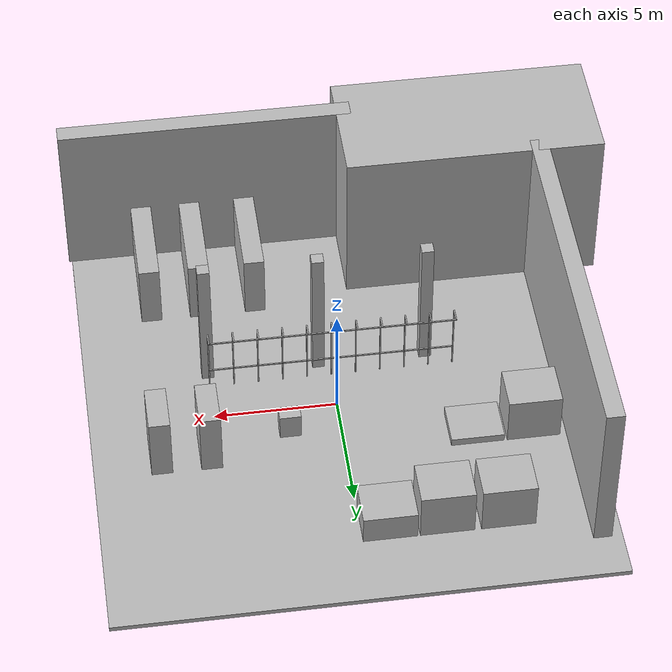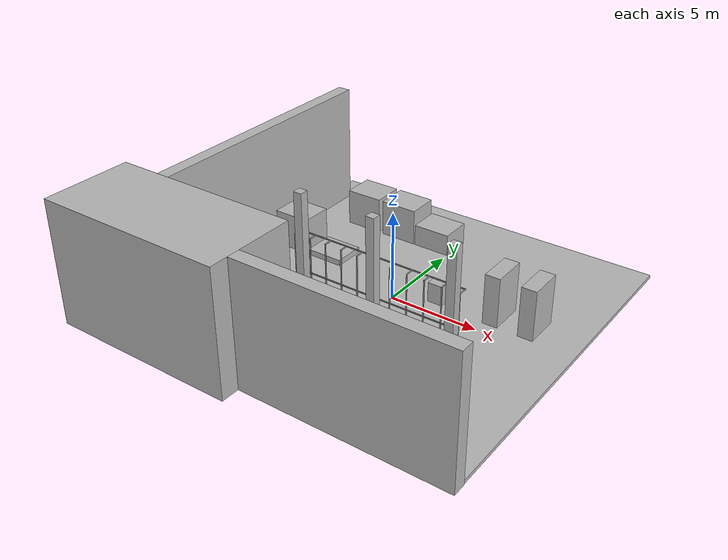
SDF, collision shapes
<?xml version='1.0'?>
<sdf version='1.6'>
  <model name='workcell'>
    <link name='link'>
      <self_collide>0</self_collide>
      <enable_wind>0</enable_wind>
      <kinematic>0</kinematic>
      <pose frame=''>0 0 0 0 -0 0</pose>
      <visual name='visual'>
        <geometry>
          <mesh>
            <uri>model://workcell/meshes/mesh.dae</uri>
          </mesh>
        </geometry>
        <material>
          <shader type='pixel'/>
        </material>
        <pose frame=''>0 0 0 0 -0 0</pose>
        <transparency>0</transparency>
        <cast_shadows>1</cast_shadows>
      </visual>
      <visual name='conveyor_frame_1'>
        <pose frame=''>0 -1.21 3 0 -0 0</pose>
        <geometry>
          <box>
            <size>10 0.05 0.05</size>
          </box>
        </geometry>
        <material>
          <ambient>0.72549 0.517647 0 1</ambient>
          <diffuse>0.72549 0.517647 0 1</diffuse>
          <shader type='pixel'/>
          <script>
            <name>ModelPreview_2::link::conveyor_frame_1_MATERIAL_</name>
            <uri>__default__</uri>
          </script>
        </material>
        <transparency>0</transparency>
        <cast_shadows>1</cast_shadows>
      </visual>
      <visual name='conveyor_frame_2'>
        <pose frame=''>0 -1.7 0.95 0 -0 0</pose>
        <geometry>
          <box>
            <size>10 0.05 0.05</size>
          </box>
        </geometry>
        <material>
          <ambient>0.72549 0.517647 0 1</ambient>
          <diffuse>0.72549 0.517647 0 1</diffuse>
          <shader type='pixel'/>
          <script>
            <name>ModelPreview_2::link::conveyor_frame_2_MATERIAL_</name>
            <uri>__default__</uri>
          </script>
        </material>
        <transparency>0</transparency>
        <cast_shadows>1</cast_shadows>
      </visual>
      <visual name='conveyor_frame_3'>
        <pose frame=''>5 -1.7 1.5 0 -0 0</pose>
        <geometry>
          <box>
            <size>0.05 0.05 3</size>
          </box>
        </geometry>
        <material>
          <ambient>0.72549 0.517647 0 1</ambient>
          <diffuse>0.72549 0.517647 0 1</diffuse>
          <shader type='pixel'/>
          <script>
            <name>ModelPreview_2::link::conveyor_frame_3_MATERIAL_</name>
            <uri>__default__</uri>
          </script>
        </material>
        <transparency>0</transparency>
        <cast_shadows>1</cast_shadows>
      </visual>
      <visual name='conveyor_frame_4'>
        <pose frame=''>5 -1.455 3 0 -0 0</pose>
        <geometry>
          <box>
            <size>0.05 0.54 0.05</size>
          </box>
        </geometry>
        <material>
          <ambient>0.72549 0.517647 0 1</ambient>
          <diffuse>0.72549 0.517647 0 1</diffuse>
          <shader type='pixel'/>
          <script>
            <name>ModelPreview_2::link::conveyor_frame_4_MATERIAL_</name>
            <uri>__default__</uri>
          </script>
        </material>
        <transparency>0</transparency>
        <cast_shadows>1</cast_shadows>
      </visual>
      <visual name='conveyor_frame_5'>
        <pose frame=''>4 -1.7 1.5 0 -0 0</pose>
        <geometry>
          <box>
            <size>0.05 0.05 3</size>
          </box>
        </geometry>
        <material>
          <ambient>0.72549 0.517647 0 1</ambient>
          <diffuse>0.72549 0.517647 0 1</diffuse>
          <shader type='pixel'/>
          <script>
            <name>ModelPreview_2::link::conveyor_frame_5_MATERIAL_</name>
            <uri>__default__</uri>
          </script>
        </material>
        <transparency>0</transparency>
        <cast_shadows>1</cast_shadows>
      </visual>
      <visual name='conveyor_frame_6'>
        <pose frame=''>4 -1.455 3 0 -0 0</pose>
        <geometry>
          <box>
            <size>0.05 0.54 0.05</size>
          </box>
        </geometry>
        <material>
          <ambient>0.72549 0.517647 0 1</ambient>
          <diffuse>0.72549 0.517647 0 1</diffuse>
          <shader type='pixel'/>
          <script>
            <name>ModelPreview_2::link::conveyor_frame_6_MATERIAL_</name>
            <uri>__default__</uri>
          </script>
        </material>
        <transparency>0</transparency>
        <cast_shadows>1</cast_shadows>
      </visual>
      <visual name='conveyor_frame_7'>
        <pose frame=''>3 -1.7 1.5 0 -0 0</pose>
        <geometry>
          <box>
            <size>0.05 0.05 3</size>
          </box>
        </geometry>
        <material>
          <ambient>0.72549 0.517647 0 1</ambient>
          <diffuse>0.72549 0.517647 0 1</diffuse>
          <shader type='pixel'/>
          <script>
            <name>ModelPreview_2::link::conveyor_frame_7_MATERIAL_</name>
            <uri>__default__</uri>
          </script>
        </material>
        <transparency>0</transparency>
        <cast_shadows>1</cast_shadows>
      </visual>
      <visual name='conveyor_frame_8'>
        <pose frame=''>3 -1.455 3 0 -0 0</pose>
        <geometry>
          <box>
            <size>0.05 0.54 0.05</size>
          </box>
        </geometry>
        <material>
          <ambient>0.72549 0.517647 0 1</ambient>
          <diffuse>0.72549 0.517647 0 1</diffuse>
          <shader type='pixel'/>
          <script>
            <name>ModelPreview_2::link::conveyor_frame_8_MATERIAL_</name>
            <uri>__default__</uri>
          </script>
        </material>
        <transparency>0</transparency>
        <cast_shadows>1</cast_shadows>
      </visual>
      <visual name='conveyor_frame_9'>
        <pose frame=''>2 -1.7 1.5 0 -0 0</pose>
        <geometry>
          <box>
            <size>0.05 0.05 3</size>
          </box>
        </geometry>
        <material>
          <ambient>0.72549 0.517647 0 1</ambient>
          <diffuse>0.72549 0.517647 0 1</diffuse>
          <shader type='pixel'/>
          <script>
            <name>ModelPreview_2::link::conveyor_frame_9_MATERIAL_</name>
            <uri>__default__</uri>
          </script>
        </material>
        <transparency>0</transparency>
        <cast_shadows>1</cast_shadows>
      </visual>
      <visual name='conveyor_frame_10'>
        <pose frame=''>2 -1.455 3 0 -0 0</pose>
        <geometry>
          <box>
            <size>0.05 0.54 0.05</size>
          </box>
        </geometry>
        <material>
          <ambient>0.72549 0.517647 0 1</ambient>
          <diffuse>0.72549 0.517647 0 1</diffuse>
          <shader type='pixel'/>
          <script>
            <name>ModelPreview_2::link::conveyor_frame_10_MATERIAL_</name>
            <uri>__default__</uri>
          </script>
        </material>
        <transparency>0</transparency>
        <cast_shadows>1</cast_shadows>
      </visual>
      <visual name='conveyor_frame_11'>
        <pose frame=''>1 -1.7 1.5 0 -0 0</pose>
        <geometry>
          <box>
            <size>0.05 0.05 3</size>
          </box>
        </geometry>
        <material>
          <ambient>0.72549 0.517647 0 1</ambient>
          <diffuse>0.72549 0.517647 0 1</diffuse>
          <shader type='pixel'/>
          <script>
            <name>ModelPreview_2::link::conveyor_frame_11_MATERIAL_</name>
            <uri>__default__</uri>
          </script>
        </material>
        <transparency>0</transparency>
        <cast_shadows>1</cast_shadows>
      </visual>
      <visual name='conveyor_frame_12'>
        <pose frame=''>1 -1.455 3 0 -0 0</pose>
        <geometry>
          <box>
            <size>0.05 0.54 0.05</size>
          </box>
        </geometry>
        <material>
          <ambient>0.72549 0.517647 0 1</ambient>
          <diffuse>0.72549 0.517647 0 1</diffuse>
          <shader type='pixel'/>
          <script>
            <name>ModelPreview_2::link::conveyor_frame_12_MATERIAL_</name>
            <uri>__default__</uri>
          </script>
        </material>
        <transparency>0</transparency>
        <cast_shadows>1</cast_shadows>
      </visual>
      <visual name='conveyor_frame_13'>
        <pose frame=''>0 -1.7 1.5 0 -0 0</pose>
        <geometry>
          <box>
            <size>0.05 0.05 3</size>
          </box>
        </geometry>
        <material>
          <ambient>0.72549 0.517647 0 1</ambient>
          <diffuse>0.72549 0.517647 0 1</diffuse>
          <shader type='pixel'/>
          <script>
            <name>ModelPreview_2::link::conveyor_frame_13_MATERIAL_</name>
            <uri>__default__</uri>
          </script>
        </material>
        <transparency>0</transparency>
        <cast_shadows>1</cast_shadows>
      </visual>
      <visual name='conveyor_frame_14'>
        <pose frame=''>0 -1.455 3 0 -0 0</pose>
        <geometry>
          <box>
            <size>0.05 0.54 0.05</size>
          </box>
        </geometry>
        <material>
          <ambient>0.72549 0.517647 0 1</ambient>
          <diffuse>0.72549 0.517647 0 1</diffuse>
          <shader type='pixel'/>
          <script>
            <name>ModelPreview_2::link::conveyor_frame_14_MATERIAL_</name>
            <uri>__default__</uri>
          </script>
        </material>
        <transparency>0</transparency>
        <cast_shadows>1</cast_shadows>
      </visual>
      <visual name='conveyor_frame_15'>
        <pose frame=''>-1 -1.7 1.5 0 -0 0</pose>
        <geometry>
          <box>
            <size>0.05 0.05 3</size>
          </box>
        </geometry>
        <material>
          <ambient>0.72549 0.517647 0 1</ambient>
          <diffuse>0.72549 0.517647 0 1</diffuse>
          <shader type='pixel'/>
          <script>
            <name>ModelPreview_2::link::conveyor_frame_15_MATERIAL_</name>
            <uri>__default__</uri>
          </script>
        </material>
        <transparency>0</transparency>
        <cast_shadows>1</cast_shadows>
      </visual>
      <visual name='conveyor_frame_16'>
        <pose frame=''>-1 -1.455 3 0 -0 0</pose>
        <geometry>
          <box>
            <size>0.05 0.54 0.05</size>
          </box>
        </geometry>
        <material>
          <ambient>0.72549 0.517647 0 1</ambient>
          <diffuse>0.72549 0.517647 0 1</diffuse>
          <shader type='pixel'/>
          <script>
            <name>ModelPreview_2::link::conveyor_frame_16_MATERIAL_</name>
            <uri>__default__</uri>
          </script>
        </material>
        <transparency>0</transparency>
        <cast_shadows>1</cast_shadows>
      </visual>
      <visual name='conveyor_frame_17'>
        <pose frame=''>-2 -1.7 1.5 0 -0 0</pose>
        <geometry>
          <box>
            <size>0.05 0.05 3</size>
          </box>
        </geometry>
        <material>
          <ambient>0.72549 0.517647 0 1</ambient>
          <diffuse>0.72549 0.517647 0 1</diffuse>
          <shader type='pixel'/>
          <script>
            <name>ModelPreview_2::link::conveyor_frame_17_MATERIAL_</name>
            <uri>__default__</uri>
          </script>
        </material>
        <transparency>0</transparency>
        <cast_shadows>1</cast_shadows>
      </visual>
      <visual name='conveyor_frame_18'>
        <pose frame=''>-2 -1.455 3 0 -0 0</pose>
        <geometry>
          <box>
            <size>0.05 0.54 0.05</size>
          </box>
        </geometry>
        <material>
          <ambient>0.72549 0.517647 0 1</ambient>
          <diffuse>0.72549 0.517647 0 1</diffuse>
          <shader type='pixel'/>
          <script>
            <name>ModelPreview_2::link::conveyor_frame_18_MATERIAL_</name>
            <uri>__default__</uri>
          </script>
        </material>
        <transparency>0</transparency>
        <cast_shadows>1</cast_shadows>
      </visual>
      <visual name='conveyor_frame_19'>
        <pose frame=''>-3 -1.7 1.5 0 -0 0</pose>
        <geometry>
          <box>
            <size>0.05 0.05 3</size>
          </box>
        </geometry>
        <material>
          <ambient>0.72549 0.517647 0 1</ambient>
          <diffuse>0.72549 0.517647 0 1</diffuse>
          <shader type='pixel'/>
          <script>
            <name>ModelPreview_2::link::conveyor_frame_19_MATERIAL_</name>
            <uri>__default__</uri>
          </script>
        </material>
        <transparency>0</transparency>
        <cast_shadows>1</cast_shadows>
      </visual>
      <visual name='conveyor_frame_20'>
        <pose frame=''>-3 -1.455 3 0 -0 0</pose>
        <geometry>
          <box>
            <size>0.05 0.54 0.05</size>
          </box>
        </geometry>
        <material>
          <ambient>0.72549 0.517647 0 1</ambient>
          <diffuse>0.72549 0.517647 0 1</diffuse>
          <shader type='pixel'/>
          <script>
            <name>ModelPreview_2::link::conveyor_frame_20_MATERIAL_</name>
            <uri>__default__</uri>
          </script>
        </material>
        <transparency>0</transparency>
        <cast_shadows>1</cast_shadows>
      </visual>
      <visual name='conveyor_frame_21'>
        <pose frame=''>-4 -1.7 1.5 0 -0 0</pose>
        <geometry>
          <box>
            <size>0.05 0.05 3</size>
          </box>
        </geometry>
        <material>
          <ambient>0.72549 0.517647 0 1</ambient>
          <diffuse>0.72549 0.517647 0 1</diffuse>
          <shader type='pixel'/>
          <script>
            <name>ModelPreview_2::link::conveyor_frame_21_MATERIAL_</name>
            <uri>__default__</uri>
          </script>
        </material>
        <transparency>0</transparency>
        <cast_shadows>1</cast_shadows>
      </visual>
      <visual name='conveyor_frame_22'>
        <pose frame=''>-4 -1.455 3 0 -0 0</pose>
        <geometry>
          <box>
            <size>0.05 0.54 0.05</size>
          </box>
        </geometry>
        <material>
          <ambient>0.72549 0.517647 0 1</ambient>
          <diffuse>0.72549 0.517647 0 1</diffuse>
          <shader type='pixel'/>
          <script>
            <name>ModelPreview_2::link::conveyor_frame_22_MATERIAL_</name>
            <uri>__default__</uri>
          </script>
        </material>
        <transparency>0</transparency>
        <cast_shadows>1</cast_shadows>
      </visual>
      <visual name='conveyor_frame_23'>
        <pose frame=''>-5 -1.7 1.5 0 -0 0</pose>
        <geometry>
          <box>
            <size>0.05 0.05 3</size>
          </box>
        </geometry>
        <material>
          <ambient>0.72549 0.517647 0 1</ambient>
          <diffuse>0.72549 0.517647 0 1</diffuse>
          <shader type='pixel'/>
          <script>
            <name>ModelPreview_2::link::conveyor_frame_23_MATERIAL_</name>
            <uri>__default__</uri>
          </script>
        </material>
        <transparency>0</transparency>
        <cast_shadows>1</cast_shadows>
      </visual>
      <visual name='conveyor_frame_24'>
        <pose frame=''>-5 -1.455 3 0 -0 0</pose>
        <geometry>
          <box>
            <size>0.05 0.54 0.05</size>
          </box>
        </geometry>
        <material>
          <ambient>0.72549 0.517647 0 1</ambient>
          <diffuse>0.72549 0.517647 0 1</diffuse>
          <shader type='pixel'/>
          <script>
            <name>ModelPreview_2::link::conveyor_frame_24_MATERIAL_</name>
            <uri>__default__</uri>
          </script>
        </material>
        <transparency>0</transparency>
        <cast_shadows>1</cast_shadows>
      </visual>
      <collision name='floor'>
        <laser_retro>0</laser_retro>
        <max_contacts>10</max_contacts>
        <pose frame=''>0 0 -0.1 0 -0 0</pose>
        <geometry>
          <box>
            <size>20.1026 20.1026 0.2</size>
          </box>
        </geometry>
        <surface>
          <friction>
            <ode>
              <mu>1</mu>
              <mu2>1</mu2>
              <fdir1>0 0 0</fdir1>
              <slip1>0</slip1>
              <slip2>0</slip2>
            </ode>
            <torsional>
              <coefficient>1</coefficient>
              <patch_radius>0</patch_radius>
              <surface_radius>0</surface_radius>
              <use_patch_radius>1</use_patch_radius>
              <ode>
                <slip>0</slip>
              </ode>
            </torsional>
          </friction>
          <bounce>
            <restitution_coefficient>0</restitution_coefficient>
            <threshold>1e+06</threshold>
          </bounce>
          <contact>
            <collide_without_contact>0</collide_without_contact>
            <collide_without_contact_bitmask>1</collide_without_contact_bitmask>
            <collide_bitmask>1</collide_bitmask>
            <ode>
              <soft_cfm>0</soft_cfm>
              <soft_erp>0.2</soft_erp>
              <kp>1e+13</kp>
              <kd>1</kd>
              <max_vel>0</max_vel>
              <min_depth>0.001</min_depth>
            </ode>
            <bullet>
              <split_impulse>1</split_impulse>
              <split_impulse_penetration_threshold>-0.01</split_impulse_penetration_threshold>
              <soft_cfm>0</soft_cfm>
              <soft_erp>0.2</soft_erp>
              <kp>1e+13</kp>
              <kd>1</kd>
            </bullet>
          </contact>
        </surface>
      </collision>
      <collision name='wall1'>
        <laser_retro>0</laser_retro>
        <max_contacts>10</max_contacts>
        <pose frame=''>4.13686 -10.0212 3.48855 0 -0 0</pose>
        <geometry>
          <box>
            <size>12.0768 0.72902 6.97771</size>
          </box>
        </geometry>
        <surface>
          <friction>
            <ode>
              <mu>1</mu>
              <mu2>1</mu2>
              <fdir1>0 0 0</fdir1>
              <slip1>0</slip1>
              <slip2>0</slip2>
            </ode>
            <torsional>
              <coefficient>1</coefficient>
              <patch_radius>0</patch_radius>
              <surface_radius>0</surface_radius>
              <use_patch_radius>1</use_patch_radius>
              <ode>
                <slip>0</slip>
              </ode>
            </torsional>
          </friction>
          <bounce>
            <restitution_coefficient>0</restitution_coefficient>
            <threshold>1e+06</threshold>
          </bounce>
          <contact>
            <collide_without_contact>0</collide_without_contact>
            <collide_without_contact_bitmask>1</collide_without_contact_bitmask>
            <collide_bitmask>1</collide_bitmask>
            <ode>
              <soft_cfm>0</soft_cfm>
              <soft_erp>0.2</soft_erp>
              <kp>1e+13</kp>
              <kd>1</kd>
              <max_vel>0.01</max_vel>
              <min_depth>0</min_depth>
            </ode>
            <bullet>
              <split_impulse>1</split_impulse>
              <split_impulse_penetration_threshold>-0.01</split_impulse_penetration_threshold>
              <soft_cfm>0</soft_cfm>
              <soft_erp>0.2</soft_erp>
              <kp>1e+13</kp>
              <kd>1</kd>
            </bullet>
          </contact>
        </surface>
      </collision>
      <collision name='wall2'>
        <laser_retro>0</laser_retro>
        <max_contacts>10</max_contacts>
        <pose frame=''>-6.58151 -8.924 3.48855 0 -0 0</pose>
        <geometry>
          <box>
            <size>10.5921 5.00198 6.97771</size>
          </box>
        </geometry>
        <surface>
          <friction>
            <ode>
              <mu>1</mu>
              <mu2>1</mu2>
              <fdir1>0 0 0</fdir1>
              <slip1>0</slip1>
              <slip2>0</slip2>
            </ode>
            <torsional>
              <coefficient>1</coefficient>
              <patch_radius>0</patch_radius>
              <surface_radius>0</surface_radius>
              <use_patch_radius>1</use_patch_radius>
              <ode>
                <slip>0</slip>
              </ode>
            </torsional>
          </friction>
          <bounce>
            <restitution_coefficient>0</restitution_coefficient>
            <threshold>1e+06</threshold>
          </bounce>
          <contact>
            <collide_without_contact>0</collide_without_contact>
            <collide_without_contact_bitmask>1</collide_without_contact_bitmask>
            <collide_bitmask>1</collide_bitmask>
            <ode>
              <soft_cfm>0</soft_cfm>
              <soft_erp>0.2</soft_erp>
              <kp>1e+13</kp>
              <kd>1</kd>
              <max_vel>0.01</max_vel>
              <min_depth>0</min_depth>
            </ode>
            <bullet>
              <split_impulse>1</split_impulse>
              <split_impulse_penetration_threshold>-0.01</split_impulse_penetration_threshold>
              <soft_cfm>0</soft_cfm>
              <soft_erp>0.2</soft_erp>
              <kp>1e+13</kp>
              <kd>1</kd>
            </bullet>
          </contact>
        </surface>
      </collision>
      <collision name='wall3'>
        <laser_retro>0</laser_retro>
        <max_contacts>10</max_contacts>
        <pose frame=''>-9.25721 0.6135 3.48855 0 -0 0</pose>
        <geometry>
          <box>
            <size>0.72902 15.2908 6.97771</size>
          </box>
        </geometry>
        <surface>
          <friction>
            <ode>
              <mu>1</mu>
              <mu2>1</mu2>
              <fdir1>0 0 0</fdir1>
              <slip1>0</slip1>
              <slip2>0</slip2>
            </ode>
            <torsional>
              <coefficient>1</coefficient>
              <patch_radius>0</patch_radius>
              <surface_radius>0</surface_radius>
              <use_patch_radius>1</use_patch_radius>
              <ode>
                <slip>0</slip>
              </ode>
            </torsional>
          </friction>
          <bounce>
            <restitution_coefficient>0</restitution_coefficient>
            <threshold>1e+06</threshold>
          </bounce>
          <contact>
            <collide_without_contact>0</collide_without_contact>
            <collide_without_contact_bitmask>1</collide_without_contact_bitmask>
            <collide_bitmask>1</collide_bitmask>
            <ode>
              <soft_cfm>0</soft_cfm>
              <soft_erp>0.2</soft_erp>
              <kp>1e+13</kp>
              <kd>1</kd>
              <max_vel>0.01</max_vel>
              <min_depth>0</min_depth>
            </ode>
            <bullet>
              <split_impulse>1</split_impulse>
              <split_impulse_penetration_threshold>-0.01</split_impulse_penetration_threshold>
              <soft_cfm>0</soft_cfm>
              <soft_erp>0.2</soft_erp>
              <kp>1e+13</kp>
              <kd>1</kd>
            </bullet>
          </contact>
        </surface>
      </collision>
      <collision name='rack1'>
        <laser_retro>0</laser_retro>
        <max_contacts>10</max_contacts>
        <pose frame=''>7.35056 1.7443 1.41643 0 -0 0</pose>
        <geometry>
          <box>
            <size>0.84444 1.95581 2.83286</size>
          </box>
        </geometry>
        <surface>
          <friction>
            <ode>
              <mu>1</mu>
              <mu2>1</mu2>
              <fdir1>0 0 0</fdir1>
              <slip1>0</slip1>
              <slip2>0</slip2>
            </ode>
            <torsional>
              <coefficient>1</coefficient>
              <patch_radius>0</patch_radius>
              <surface_radius>0</surface_radius>
              <use_patch_radius>1</use_patch_radius>
              <ode>
                <slip>0</slip>
              </ode>
            </torsional>
          </friction>
          <bounce>
            <restitution_coefficient>0</restitution_coefficient>
            <threshold>1e+06</threshold>
          </bounce>
          <contact>
            <collide_without_contact>0</collide_without_contact>
            <collide_without_contact_bitmask>1</collide_without_contact_bitmask>
            <collide_bitmask>1</collide_bitmask>
            <ode>
              <soft_cfm>0</soft_cfm>
              <soft_erp>0.2</soft_erp>
              <kp>1e+13</kp>
              <kd>1</kd>
              <max_vel>0.01</max_vel>
              <min_depth>0</min_depth>
            </ode>
            <bullet>
              <split_impulse>1</split_impulse>
              <split_impulse_penetration_threshold>-0.01</split_impulse_penetration_threshold>
              <soft_cfm>0</soft_cfm>
              <soft_erp>0.2</soft_erp>
              <kp>1e+13</kp>
              <kd>1</kd>
            </bullet>
          </contact>
        </surface>
      </collision>
      <collision name='rack2'>
        <laser_retro>0</laser_retro>
        <max_contacts>10</max_contacts>
        <pose frame=''>5.36795 1.7443 1.41643 0 -0 0</pose>
        <geometry>
          <box>
            <size>0.84444 1.95581 2.83286</size>
          </box>
        </geometry>
        <surface>
          <friction>
            <ode>
              <mu>1</mu>
              <mu2>1</mu2>
              <fdir1>0 0 0</fdir1>
              <slip1>0</slip1>
              <slip2>0</slip2>
            </ode>
            <torsional>
              <coefficient>1</coefficient>
              <patch_radius>0</patch_radius>
              <surface_radius>0</surface_radius>
              <use_patch_radius>1</use_patch_radius>
              <ode>
                <slip>0</slip>
              </ode>
            </torsional>
          </friction>
          <bounce>
            <restitution_coefficient>0</restitution_coefficient>
            <threshold>1e+06</threshold>
          </bounce>
          <contact>
            <collide_without_contact>0</collide_without_contact>
            <collide_without_contact_bitmask>1</collide_without_contact_bitmask>
            <collide_bitmask>1</collide_bitmask>
            <ode>
              <soft_cfm>0</soft_cfm>
              <soft_erp>0.2</soft_erp>
              <kp>1e+13</kp>
              <kd>1</kd>
              <max_vel>0.01</max_vel>
              <min_depth>0</min_depth>
            </ode>
            <bullet>
              <split_impulse>1</split_impulse>
              <split_impulse_penetration_threshold>-0.01</split_impulse_penetration_threshold>
              <soft_cfm>0</soft_cfm>
              <soft_erp>0.2</soft_erp>
              <kp>1e+13</kp>
              <kd>1</kd>
            </bullet>
          </contact>
        </surface>
      </collision>
      <collision name='rack3'>
        <laser_retro>0</laser_retro>
        <max_contacts>10</max_contacts>
        <pose frame=''>7.00142 -7.6467 1.41643 0 -0 0</pose>
        <geometry>
          <box>
            <size>0.84444 3.91162 2.83286</size>
          </box>
        </geometry>
        <surface>
          <friction>
            <ode>
              <mu>1</mu>
              <mu2>1</mu2>
              <fdir1>0 0 0</fdir1>
              <slip1>0</slip1>
              <slip2>0</slip2>
            </ode>
            <torsional>
              <coefficient>1</coefficient>
              <patch_radius>0</patch_radius>
              <surface_radius>0</surface_radius>
              <use_patch_radius>1</use_patch_radius>
              <ode>
                <slip>0</slip>
              </ode>
            </torsional>
          </friction>
          <bounce>
            <restitution_coefficient>0</restitution_coefficient>
            <threshold>1e+06</threshold>
          </bounce>
          <contact>
            <collide_without_contact>0</collide_without_contact>
            <collide_without_contact_bitmask>1</collide_without_contact_bitmask>
            <collide_bitmask>1</collide_bitmask>
            <ode>
              <soft_cfm>0</soft_cfm>
              <soft_erp>0.2</soft_erp>
              <kp>1e+13</kp>
              <kd>1</kd>
              <max_vel>0.01</max_vel>
              <min_depth>0</min_depth>
            </ode>
            <bullet>
              <split_impulse>1</split_impulse>
              <split_impulse_penetration_threshold>-0.01</split_impulse_penetration_threshold>
              <soft_cfm>0</soft_cfm>
              <soft_erp>0.2</soft_erp>
              <kp>1e+13</kp>
              <kd>1</kd>
            </bullet>
          </contact>
        </surface>
      </collision>
      <collision name='rack4'>
        <laser_retro>0</laser_retro>
        <max_contacts>10</max_contacts>
        <pose frame=''>4.97338 -7.6467 1.41643 0 -0 0</pose>
        <geometry>
          <box>
            <size>0.84444 3.91162 2.83286</size>
          </box>
        </geometry>
        <surface>
          <friction>
            <ode>
              <mu>1</mu>
              <mu2>1</mu2>
              <fdir1>0 0 0</fdir1>
              <slip1>0</slip1>
              <slip2>0</slip2>
            </ode>
            <torsional>
              <coefficient>1</coefficient>
              <patch_radius>0</patch_radius>
              <surface_radius>0</surface_radius>
              <use_patch_radius>1</use_patch_radius>
              <ode>
                <slip>0</slip>
              </ode>
            </torsional>
          </friction>
          <bounce>
            <restitution_coefficient>0</restitution_coefficient>
            <threshold>1e+06</threshold>
          </bounce>
          <contact>
            <collide_without_contact>0</collide_without_contact>
            <collide_without_contact_bitmask>1</collide_without_contact_bitmask>
            <collide_bitmask>1</collide_bitmask>
            <ode>
              <soft_cfm>0</soft_cfm>
              <soft_erp>0.2</soft_erp>
              <kp>1e+13</kp>
              <kd>1</kd>
              <max_vel>0.01</max_vel>
              <min_depth>0</min_depth>
            </ode>
            <bullet>
              <split_impulse>1</split_impulse>
              <split_impulse_penetration_threshold>-0.01</split_impulse_penetration_threshold>
              <soft_cfm>0</soft_cfm>
              <soft_erp>0.2</soft_erp>
              <kp>1e+13</kp>
              <kd>1</kd>
            </bullet>
          </contact>
        </surface>
      </collision>
      <collision name='rack5'>
        <laser_retro>0</laser_retro>
        <max_contacts>10</max_contacts>
        <pose frame=''>2.66949 -7.6467 1.41643 0 -0 0</pose>
        <geometry>
          <box>
            <size>0.84444 3.91162 2.83286</size>
          </box>
        </geometry>
        <surface>
          <friction>
            <ode>
              <mu>1</mu>
              <mu2>1</mu2>
              <fdir1>0 0 0</fdir1>
              <slip1>0</slip1>
              <slip2>0</slip2>
            </ode>
            <torsional>
              <coefficient>1</coefficient>
              <patch_radius>0</patch_radius>
              <surface_radius>0</surface_radius>
              <use_patch_radius>1</use_patch_radius>
              <ode>
                <slip>0</slip>
              </ode>
            </torsional>
          </friction>
          <bounce>
            <restitution_coefficient>0</restitution_coefficient>
            <threshold>1e+06</threshold>
          </bounce>
          <contact>
            <collide_without_contact>0</collide_without_contact>
            <collide_without_contact_bitmask>1</collide_without_contact_bitmask>
            <collide_bitmask>1</collide_bitmask>
            <ode>
              <soft_cfm>0</soft_cfm>
              <soft_erp>0.2</soft_erp>
              <kp>1e+13</kp>
              <kd>1</kd>
              <max_vel>0.01</max_vel>
              <min_depth>0</min_depth>
            </ode>
            <bullet>
              <split_impulse>1</split_impulse>
              <split_impulse_penetration_threshold>-0.01</split_impulse_penetration_threshold>
              <soft_cfm>0</soft_cfm>
              <soft_erp>0.2</soft_erp>
              <kp>1e+13</kp>
              <kd>1</kd>
            </bullet>
          </contact>
        </surface>
      </collision>
      <collision name='large_pallet1'>
        <laser_retro>0</laser_retro>
        <max_contacts>10</max_contacts>
        <pose frame=''>-3.33609 6.31883 1.04257 0 -0 0</pose>
        <geometry>
          <box>
            <size>2.14726 1.79349 2.08514</size>
          </box>
        </geometry>
        <surface>
          <friction>
            <ode>
              <mu>1</mu>
              <mu2>1</mu2>
              <fdir1>0 0 0</fdir1>
              <slip1>0</slip1>
              <slip2>0</slip2>
            </ode>
            <torsional>
              <coefficient>1</coefficient>
              <patch_radius>0</patch_radius>
              <surface_radius>0</surface_radius>
              <use_patch_radius>1</use_patch_radius>
              <ode>
                <slip>0</slip>
              </ode>
            </torsional>
          </friction>
          <bounce>
            <restitution_coefficient>0</restitution_coefficient>
            <threshold>1e+06</threshold>
          </bounce>
          <contact>
            <collide_without_contact>0</collide_without_contact>
            <collide_without_contact_bitmask>1</collide_without_contact_bitmask>
            <collide_bitmask>1</collide_bitmask>
            <ode>
              <soft_cfm>0</soft_cfm>
              <soft_erp>0.2</soft_erp>
              <kp>1e+13</kp>
              <kd>1</kd>
              <max_vel>0.01</max_vel>
              <min_depth>0</min_depth>
            </ode>
            <bullet>
              <split_impulse>1</split_impulse>
              <split_impulse_penetration_threshold>-0.01</split_impulse_penetration_threshold>
              <soft_cfm>0</soft_cfm>
              <soft_erp>0.2</soft_erp>
              <kp>1e+13</kp>
              <kd>1</kd>
            </bullet>
          </contact>
        </surface>
      </collision>
      <collision name='large_pallet2'>
        <laser_retro>0</laser_retro>
        <max_contacts>10</max_contacts>
        <pose frame=''>-5.74492 6.31883 1.04257 0 -0 0</pose>
        <geometry>
          <box>
            <size>2.14726 1.79349 2.08514</size>
          </box>
        </geometry>
        <surface>
          <friction>
            <ode>
              <mu>1</mu>
              <mu2>1</mu2>
              <fdir1>0 0 0</fdir1>
              <slip1>0</slip1>
              <slip2>0</slip2>
            </ode>
            <torsional>
              <coefficient>1</coefficient>
              <patch_radius>0</patch_radius>
              <surface_radius>0</surface_radius>
              <use_patch_radius>1</use_patch_radius>
              <ode>
                <slip>0</slip>
              </ode>
            </torsional>
          </friction>
          <bounce>
            <restitution_coefficient>0</restitution_coefficient>
            <threshold>1e+06</threshold>
          </bounce>
          <contact>
            <collide_without_contact>0</collide_without_contact>
            <collide_without_contact_bitmask>1</collide_without_contact_bitmask>
            <collide_bitmask>1</collide_bitmask>
            <ode>
              <soft_cfm>0</soft_cfm>
              <soft_erp>0.2</soft_erp>
              <kp>1e+13</kp>
              <kd>1</kd>
              <max_vel>0.01</max_vel>
              <min_depth>0</min_depth>
            </ode>
            <bullet>
              <split_impulse>1</split_impulse>
              <split_impulse_penetration_threshold>-0.01</split_impulse_penetration_threshold>
              <soft_cfm>0</soft_cfm>
              <soft_erp>0.2</soft_erp>
              <kp>1e+13</kp>
              <kd>1</kd>
            </bullet>
          </contact>
        </surface>
      </collision>
      <collision name='large_pallet3'>
        <laser_retro>0</laser_retro>
        <max_contacts>10</max_contacts>
        <pose frame=''>-7.55868 1.91644 1.04257 0 -0 0</pose>
        <geometry>
          <box>
            <size>2.14726 1.79432 2.08514</size>
          </box>
        </geometry>
        <surface>
          <friction>
            <ode>
              <mu>1</mu>
              <mu2>1</mu2>
              <fdir1>0 0 0</fdir1>
              <slip1>0</slip1>
              <slip2>0</slip2>
            </ode>
            <torsional>
              <coefficient>1</coefficient>
              <patch_radius>0</patch_radius>
              <surface_radius>0</surface_radius>
              <use_patch_radius>1</use_patch_radius>
              <ode>
                <slip>0</slip>
              </ode>
            </torsional>
          </friction>
          <bounce>
            <restitution_coefficient>0</restitution_coefficient>
            <threshold>1e+06</threshold>
          </bounce>
          <contact>
            <collide_without_contact>0</collide_without_contact>
            <collide_without_contact_bitmask>1</collide_without_contact_bitmask>
            <collide_bitmask>1</collide_bitmask>
            <ode>
              <soft_cfm>0</soft_cfm>
              <soft_erp>0.2</soft_erp>
              <kp>1e+13</kp>
              <kd>1</kd>
              <max_vel>0.01</max_vel>
              <min_depth>0</min_depth>
            </ode>
            <bullet>
              <split_impulse>1</split_impulse>
              <split_impulse_penetration_threshold>-0.01</split_impulse_penetration_threshold>
              <soft_cfm>0</soft_cfm>
              <soft_erp>0.2</soft_erp>
              <kp>1e+13</kp>
              <kd>1</kd>
            </bullet>
          </contact>
        </surface>
      </collision>
      <collision name='empty_pallet1'>
        <laser_retro>0</laser_retro>
        <max_contacts>10</max_contacts>
        <pose frame=''>-5.29667 1.91644 0.1636 0 -0 0</pose>
        <geometry>
          <box>
            <size>2.14726 1.79349 0.3272</size>
          </box>
        </geometry>
        <surface>
          <friction>
            <ode>
              <mu>1</mu>
              <mu2>1</mu2>
              <fdir1>0 0 0</fdir1>
              <slip1>0</slip1>
              <slip2>0</slip2>
            </ode>
            <torsional>
              <coefficient>1</coefficient>
              <patch_radius>0</patch_radius>
              <surface_radius>0</surface_radius>
              <use_patch_radius>1</use_patch_radius>
              <ode>
                <slip>0</slip>
              </ode>
            </torsional>
          </friction>
          <bounce>
            <restitution_coefficient>0</restitution_coefficient>
            <threshold>1e+06</threshold>
          </bounce>
          <contact>
            <collide_without_contact>0</collide_without_contact>
            <collide_without_contact_bitmask>1</collide_without_contact_bitmask>
            <collide_bitmask>1</collide_bitmask>
            <ode>
              <soft_cfm>0</soft_cfm>
              <soft_erp>0.2</soft_erp>
              <kp>1e+13</kp>
              <kd>1</kd>
              <max_vel>0.01</max_vel>
              <min_depth>0</min_depth>
            </ode>
            <bullet>
              <split_impulse>1</split_impulse>
              <split_impulse_penetration_threshold>-0.01</split_impulse_penetration_threshold>
              <soft_cfm>0</soft_cfm>
              <soft_erp>0.2</soft_erp>
              <kp>1e+13</kp>
              <kd>1</kd>
            </bullet>
          </contact>
        </surface>
      </collision>
      <collision name='box_pallet1'>
        <laser_retro>0</laser_retro>
        <max_contacts>10</max_contacts>
        <pose frame=''>-1.09806 6.31883 0.61958 0 -0 0</pose>
        <geometry>
          <box>
            <size>2.14726 1.79349 1.23916</size>
          </box>
        </geometry>
        <surface>
          <friction>
            <ode>
              <mu>1</mu>
              <mu2>1</mu2>
              <fdir1>0 0 0</fdir1>
              <slip1>0</slip1>
              <slip2>0</slip2>
            </ode>
            <torsional>
              <coefficient>1</coefficient>
              <patch_radius>0</patch_radius>
              <surface_radius>0</surface_radius>
              <use_patch_radius>1</use_patch_radius>
              <ode>
                <slip>0</slip>
              </ode>
            </torsional>
          </friction>
          <bounce>
            <restitution_coefficient>0</restitution_coefficient>
            <threshold>1e+06</threshold>
          </bounce>
          <contact>
            <collide_without_contact>0</collide_without_contact>
            <collide_without_contact_bitmask>1</collide_without_contact_bitmask>
            <collide_bitmask>1</collide_bitmask>
            <ode>
              <soft_cfm>0</soft_cfm>
              <soft_erp>0.2</soft_erp>
              <kp>1e+13</kp>
              <kd>1</kd>
              <max_vel>0.01</max_vel>
              <min_depth>0</min_depth>
            </ode>
            <bullet>
              <split_impulse>1</split_impulse>
              <split_impulse_penetration_threshold>-0.01</split_impulse_penetration_threshold>
              <soft_cfm>0</soft_cfm>
              <soft_erp>0.2</soft_erp>
              <kp>1e+13</kp>
              <kd>1</kd>
            </bullet>
          </contact>
        </surface>
      </collision>
      <collision name='pole1'>
        <laser_retro>0</laser_retro>
        <max_contacts>10</max_contacts>
        <pose frame=''>5.02174 -2.39478 3.02208 0 -0 0</pose>
        <geometry>
          <box>
            <size>0.49161 0.49161 6.04415</size>
          </box>
        </geometry>
        <surface>
          <friction>
            <ode>
              <mu>1</mu>
              <mu2>1</mu2>
              <fdir1>0 0 0</fdir1>
              <slip1>0</slip1>
              <slip2>0</slip2>
            </ode>
            <torsional>
              <coefficient>1</coefficient>
              <patch_radius>0</patch_radius>
              <surface_radius>0</surface_radius>
              <use_patch_radius>1</use_patch_radius>
              <ode>
                <slip>0</slip>
              </ode>
            </torsional>
          </friction>
          <bounce>
            <restitution_coefficient>0</restitution_coefficient>
            <threshold>1e+06</threshold>
          </bounce>
          <contact>
            <collide_without_contact>0</collide_without_contact>
            <collide_without_contact_bitmask>1</collide_without_contact_bitmask>
            <collide_bitmask>1</collide_bitmask>
            <ode>
              <soft_cfm>0</soft_cfm>
              <soft_erp>0.2</soft_erp>
              <kp>1e+13</kp>
              <kd>1</kd>
              <max_vel>0.01</max_vel>
              <min_depth>0</min_depth>
            </ode>
            <bullet>
              <split_impulse>1</split_impulse>
              <split_impulse_penetration_threshold>-0.01</split_impulse_penetration_threshold>
              <soft_cfm>0</soft_cfm>
              <soft_erp>0.2</soft_erp>
              <kp>1e+13</kp>
              <kd>1</kd>
            </bullet>
          </contact>
        </surface>
      </collision>
      <collision name='pole2'>
        <laser_retro>0</laser_retro>
        <max_contacts>10</max_contacts>
        <pose frame=''>0.47071 -2.39478 3.02208 0 -0 0</pose>
        <geometry>
          <box>
            <size>0.49161 0.49161 6.04415</size>
          </box>
        </geometry>
        <surface>
          <friction>
            <ode>
              <mu>1</mu>
              <mu2>1</mu2>
              <fdir1>0 0 0</fdir1>
              <slip1>0</slip1>
              <slip2>0</slip2>
            </ode>
            <torsional>
              <coefficient>1</coefficient>
              <patch_radius>0</patch_radius>
              <surface_radius>0</surface_radius>
              <use_patch_radius>1</use_patch_radius>
              <ode>
                <slip>0</slip>
              </ode>
            </torsional>
          </friction>
          <bounce>
            <restitution_coefficient>0</restitution_coefficient>
            <threshold>1e+06</threshold>
          </bounce>
          <contact>
            <collide_without_contact>0</collide_without_contact>
            <collide_without_contact_bitmask>1</collide_without_contact_bitmask>
            <collide_bitmask>1</collide_bitmask>
            <ode>
              <soft_cfm>0</soft_cfm>
              <soft_erp>0.2</soft_erp>
              <kp>1e+13</kp>
              <kd>1</kd>
              <max_vel>0.01</max_vel>
              <min_depth>0</min_depth>
            </ode>
            <bullet>
              <split_impulse>1</split_impulse>
              <split_impulse_penetration_threshold>-0.01</split_impulse_penetration_threshold>
              <soft_cfm>0</soft_cfm>
              <soft_erp>0.2</soft_erp>
              <kp>1e+13</kp>
              <kd>1</kd>
            </bullet>
          </contact>
        </surface>
      </collision>
      <collision name='pole3'>
        <laser_retro>0</laser_retro>
        <max_contacts>10</max_contacts>
        <pose frame=''>-3.93786 -2.39478 3.02208 0 -0 0</pose>
        <geometry>
          <box>
            <size>0.49161 0.49161 6.04415</size>
          </box>
        </geometry>
        <surface>
          <friction>
            <ode>
              <mu>1</mu>
              <mu2>1</mu2>
              <fdir1>0 0 0</fdir1>
              <slip1>0</slip1>
              <slip2>0</slip2>
            </ode>
            <torsional>
              <coefficient>1</coefficient>
              <patch_radius>0</patch_radius>
              <surface_radius>0</surface_radius>
              <use_patch_radius>1</use_patch_radius>
              <ode>
                <slip>0</slip>
              </ode>
            </torsional>
          </friction>
          <bounce>
            <restitution_coefficient>0</restitution_coefficient>
            <threshold>1e+06</threshold>
          </bounce>
          <contact>
            <collide_without_contact>0</collide_without_contact>
            <collide_without_contact_bitmask>1</collide_without_contact_bitmask>
            <collide_bitmask>1</collide_bitmask>
            <ode>
              <soft_cfm>0</soft_cfm>
              <soft_erp>0.2</soft_erp>
              <kp>1e+13</kp>
              <kd>1</kd>
              <max_vel>0.01</max_vel>
              <min_depth>0</min_depth>
            </ode>
            <bullet>
              <split_impulse>1</split_impulse>
              <split_impulse_penetration_threshold>-0.01</split_impulse_penetration_threshold>
              <soft_cfm>0</soft_cfm>
              <soft_erp>0.2</soft_erp>
              <kp>1e+13</kp>
              <kd>1</kd>
            </bullet>
          </contact>
        </surface>
      </collision>
      <collision name='conveyor_frame_1_collision'>
        <laser_retro>0</laser_retro>
        <max_contacts>10</max_contacts>
        <pose frame=''>0 -1.21 3 0 -0 0</pose>
        <geometry>
          <box>
            <size>10 0.05 0.05</size>
          </box>
        </geometry>
        <surface>
          <friction>
            <ode>
              <mu>1</mu>
              <mu2>1</mu2>
              <fdir1>0 0 0</fdir1>
              <slip1>0</slip1>
              <slip2>0</slip2>
            </ode>
            <torsional>
              <coefficient>1</coefficient>
              <patch_radius>0</patch_radius>
              <surface_radius>0</surface_radius>
              <use_patch_radius>1</use_patch_radius>
              <ode>
                <slip>0</slip>
              </ode>
            </torsional>
          </friction>
          <bounce>
            <restitution_coefficient>0</restitution_coefficient>
            <threshold>1e+06</threshold>
          </bounce>
          <contact>
            <collide_without_contact>0</collide_without_contact>
            <collide_without_contact_bitmask>1</collide_without_contact_bitmask>
            <collide_bitmask>1</collide_bitmask>
            <ode>
              <soft_cfm>0</soft_cfm>
              <soft_erp>0.2</soft_erp>
              <kp>1e+13</kp>
              <kd>1</kd>
              <max_vel>0.01</max_vel>
              <min_depth>0</min_depth>
            </ode>
            <bullet>
              <split_impulse>1</split_impulse>
              <split_impulse_penetration_threshold>-0.01</split_impulse_penetration_threshold>
              <soft_cfm>0</soft_cfm>
              <soft_erp>0.2</soft_erp>
              <kp>1e+13</kp>
              <kd>1</kd>
            </bullet>
          </contact>
        </surface>
      </collision>
      <collision name='control_panel'>
        <laser_retro>0</laser_retro>
        <max_contacts>10</max_contacts>
        <pose frame=''>2.07015 1.16224 0.561315 0 -0 0</pose>
        <geometry>
          <box>
            <size>0.86733 0.6001 1.12263</size>
          </box>
        </geometry>
        <surface>
          <friction>
            <ode>
              <mu>1</mu>
              <mu2>1</mu2>
              <fdir1>0 0 0</fdir1>
              <slip1>0</slip1>
              <slip2>0</slip2>
            </ode>
            <torsional>
              <coefficient>1</coefficient>
              <patch_radius>0</patch_radius>
              <surface_radius>0</surface_radius>
              <use_patch_radius>1</use_patch_radius>
              <ode>
                <slip>0</slip>
              </ode>
            </torsional>
          </friction>
          <bounce>
            <restitution_coefficient>0</restitution_coefficient>
            <threshold>1e+06</threshold>
          </bounce>
          <contact>
            <collide_without_contact>0</collide_without_contact>
            <collide_without_contact_bitmask>1</collide_without_contact_bitmask>
            <collide_bitmask>1</collide_bitmask>
            <ode>
              <soft_cfm>0</soft_cfm>
              <soft_erp>0.2</soft_erp>
              <kp>1e+13</kp>
              <kd>1</kd>
              <max_vel>0.01</max_vel>
              <min_depth>0</min_depth>
            </ode>
            <bullet>
              <split_impulse>1</split_impulse>
              <split_impulse_penetration_threshold>-0.01</split_impulse_penetration_threshold>
              <soft_cfm>0</soft_cfm>
              <soft_erp>0.2</soft_erp>
              <kp>1e+13</kp>
              <kd>1</kd>
            </bullet>
          </contact>
        </surface>
      </collision>
      <collision name='conveyor_frame_3_collision'>
        <laser_retro>0</laser_retro>
        <max_contacts>10</max_contacts>
        <pose frame=''>5 -1.7 1.5 0 -0 0</pose>
        <geometry>
          <box>
            <size>0.05 0.05 3</size>
          </box>
        </geometry>
        <surface>
          <friction>
            <ode>
              <mu>1</mu>
              <mu2>1</mu2>
              <fdir1>0 0 0</fdir1>
              <slip1>0</slip1>
              <slip2>0</slip2>
            </ode>
            <torsional>
              <coefficient>1</coefficient>
              <patch_radius>0</patch_radius>
              <surface_radius>0</surface_radius>
              <use_patch_radius>1</use_patch_radius>
              <ode>
                <slip>0</slip>
              </ode>
            </torsional>
          </friction>
          <bounce>
            <restitution_coefficient>0</restitution_coefficient>
            <threshold>1e+06</threshold>
          </bounce>
          <contact>
            <collide_without_contact>0</collide_without_contact>
            <collide_without_contact_bitmask>1</collide_without_contact_bitmask>
            <collide_bitmask>1</collide_bitmask>
            <ode>
              <soft_cfm>0</soft_cfm>
              <soft_erp>0.2</soft_erp>
              <kp>1e+13</kp>
              <kd>1</kd>
              <max_vel>0.01</max_vel>
              <min_depth>0</min_depth>
            </ode>
            <bullet>
              <split_impulse>1</split_impulse>
              <split_impulse_penetration_threshold>-0.01</split_impulse_penetration_threshold>
              <soft_cfm>0</soft_cfm>
              <soft_erp>0.2</soft_erp>
              <kp>1e+13</kp>
              <kd>1</kd>
            </bullet>
          </contact>
        </surface>
      </collision>
      <collision name='conveyor_frame_2_collision'>
        <laser_retro>0</laser_retro>
        <max_contacts>10</max_contacts>
        <pose frame=''>0 -1.7 0.95 0 -0 0</pose>
        <geometry>
          <box>
            <size>10 0.05 0.05</size>
          </box>
        </geometry>
        <surface>
          <friction>
            <ode>
              <mu>1</mu>
              <mu2>1</mu2>
              <fdir1>0 0 0</fdir1>
              <slip1>0</slip1>
              <slip2>0</slip2>
            </ode>
            <torsional>
              <coefficient>1</coefficient>
              <patch_radius>0</patch_radius>
              <surface_radius>0</surface_radius>
              <use_patch_radius>1</use_patch_radius>
              <ode>
                <slip>0</slip>
              </ode>
            </torsional>
          </friction>
          <bounce>
            <restitution_coefficient>0</restitution_coefficient>
            <threshold>1e+06</threshold>
          </bounce>
          <contact>
            <collide_without_contact>0</collide_without_contact>
            <collide_without_contact_bitmask>1</collide_without_contact_bitmask>
            <collide_bitmask>1</collide_bitmask>
            <ode>
              <soft_cfm>0</soft_cfm>
              <soft_erp>0.2</soft_erp>
              <kp>1e+13</kp>
              <kd>1</kd>
              <max_vel>0.01</max_vel>
              <min_depth>0</min_depth>
            </ode>
            <bullet>
              <split_impulse>1</split_impulse>
              <split_impulse_penetration_threshold>-0.01</split_impulse_penetration_threshold>
              <soft_cfm>0</soft_cfm>
              <soft_erp>0.2</soft_erp>
              <kp>1e+13</kp>
              <kd>1</kd>
            </bullet>
          </contact>
        </surface>
      </collision>
      <collision name='conveyor_frame_3_collision'>
        <laser_retro>0</laser_retro>
        <max_contacts>10</max_contacts>
        <pose frame=''>5 -1.455 3 0 -0 0</pose>
        <geometry>
          <box>
            <size>0.05 0.54 0.05</size>
          </box>
        </geometry>
        <surface>
          <friction>
            <ode>
              <mu>1</mu>
              <mu2>1</mu2>
              <fdir1>0 0 0</fdir1>
              <slip1>0</slip1>
              <slip2>0</slip2>
            </ode>
            <torsional>
              <coefficient>1</coefficient>
              <patch_radius>0</patch_radius>
              <surface_radius>0</surface_radius>
              <use_patch_radius>1</use_patch_radius>
              <ode>
                <slip>0</slip>
              </ode>
            </torsional>
          </friction>
          <bounce>
            <restitution_coefficient>0</restitution_coefficient>
            <threshold>1e+06</threshold>
          </bounce>
          <contact>
            <collide_without_contact>0</collide_without_contact>
            <collide_without_contact_bitmask>1</collide_without_contact_bitmask>
            <collide_bitmask>1</collide_bitmask>
            <ode>
              <soft_cfm>0</soft_cfm>
              <soft_erp>0.2</soft_erp>
              <kp>1e+13</kp>
              <kd>1</kd>
              <max_vel>0.01</max_vel>
              <min_depth>0</min_depth>
            </ode>
            <bullet>
              <split_impulse>1</split_impulse>
              <split_impulse_penetration_threshold>-0.01</split_impulse_penetration_threshold>
              <soft_cfm>0</soft_cfm>
              <soft_erp>0.2</soft_erp>
              <kp>1e+13</kp>
              <kd>1</kd>
            </bullet>
          </contact>
        </surface>
      </collision>
      <collision name='conveyor_frame_5_collision'>
        <laser_retro>0</laser_retro>
        <max_contacts>10</max_contacts>
        <pose frame=''>4 -1.7 1.5 0 -0 0</pose>
        <geometry>
          <box>
            <size>0.05 0.05 3</size>
          </box>
        </geometry>
        <surface>
          <friction>
            <ode>
              <mu>1</mu>
              <mu2>1</mu2>
              <fdir1>0 0 0</fdir1>
              <slip1>0</slip1>
              <slip2>0</slip2>
            </ode>
            <torsional>
              <coefficient>1</coefficient>
              <patch_radius>0</patch_radius>
              <surface_radius>0</surface_radius>
              <use_patch_radius>1</use_patch_radius>
              <ode>
                <slip>0</slip>
              </ode>
            </torsional>
          </friction>
          <bounce>
            <restitution_coefficient>0</restitution_coefficient>
            <threshold>1e+06</threshold>
          </bounce>
          <contact>
            <collide_without_contact>0</collide_without_contact>
            <collide_without_contact_bitmask>1</collide_without_contact_bitmask>
            <collide_bitmask>1</collide_bitmask>
            <ode>
              <soft_cfm>0</soft_cfm>
              <soft_erp>0.2</soft_erp>
              <kp>1e+13</kp>
              <kd>1</kd>
              <max_vel>0.01</max_vel>
              <min_depth>0</min_depth>
            </ode>
            <bullet>
              <split_impulse>1</split_impulse>
              <split_impulse_penetration_threshold>-0.01</split_impulse_penetration_threshold>
              <soft_cfm>0</soft_cfm>
              <soft_erp>0.2</soft_erp>
              <kp>1e+13</kp>
              <kd>1</kd>
            </bullet>
          </contact>
        </surface>
      </collision>
      <collision name='conveyor_frame_6_collision'>
        <laser_retro>0</laser_retro>
        <max_contacts>10</max_contacts>
        <pose frame=''>4 -1.455 3 0 -0 0</pose>
        <geometry>
          <box>
            <size>0.05 0.54 0.05</size>
          </box>
        </geometry>
        <surface>
          <friction>
            <ode>
              <mu>1</mu>
              <mu2>1</mu2>
              <fdir1>0 0 0</fdir1>
              <slip1>0</slip1>
              <slip2>0</slip2>
            </ode>
            <torsional>
              <coefficient>1</coefficient>
              <patch_radius>0</patch_radius>
              <surface_radius>0</surface_radius>
              <use_patch_radius>1</use_patch_radius>
              <ode>
                <slip>0</slip>
              </ode>
            </torsional>
          </friction>
          <bounce>
            <restitution_coefficient>0</restitution_coefficient>
            <threshold>1e+06</threshold>
          </bounce>
          <contact>
            <collide_without_contact>0</collide_without_contact>
            <collide_without_contact_bitmask>1</collide_without_contact_bitmask>
            <collide_bitmask>1</collide_bitmask>
            <ode>
              <soft_cfm>0</soft_cfm>
              <soft_erp>0.2</soft_erp>
              <kp>1e+13</kp>
              <kd>1</kd>
              <max_vel>0.01</max_vel>
              <min_depth>0</min_depth>
            </ode>
            <bullet>
              <split_impulse>1</split_impulse>
              <split_impulse_penetration_threshold>-0.01</split_impulse_penetration_threshold>
              <soft_cfm>0</soft_cfm>
              <soft_erp>0.2</soft_erp>
              <kp>1e+13</kp>
              <kd>1</kd>
            </bullet>
          </contact>
        </surface>
      </collision>
      <collision name='conveyor_frame_7_collision'>
        <laser_retro>0</laser_retro>
        <max_contacts>10</max_contacts>
        <pose frame=''>3 -1.7 1.5 0 -0 0</pose>
        <geometry>
          <box>
            <size>0.05 0.05 3</size>
          </box>
        </geometry>
        <surface>
          <friction>
            <ode>
              <mu>1</mu>
              <mu2>1</mu2>
              <fdir1>0 0 0</fdir1>
              <slip1>0</slip1>
              <slip2>0</slip2>
            </ode>
            <torsional>
              <coefficient>1</coefficient>
              <patch_radius>0</patch_radius>
              <surface_radius>0</surface_radius>
              <use_patch_radius>1</use_patch_radius>
              <ode>
                <slip>0</slip>
              </ode>
            </torsional>
          </friction>
          <bounce>
            <restitution_coefficient>0</restitution_coefficient>
            <threshold>1e+06</threshold>
          </bounce>
          <contact>
            <collide_without_contact>0</collide_without_contact>
            <collide_without_contact_bitmask>1</collide_without_contact_bitmask>
            <collide_bitmask>1</collide_bitmask>
            <ode>
              <soft_cfm>0</soft_cfm>
              <soft_erp>0.2</soft_erp>
              <kp>1e+13</kp>
              <kd>1</kd>
              <max_vel>0.01</max_vel>
              <min_depth>0</min_depth>
            </ode>
            <bullet>
              <split_impulse>1</split_impulse>
              <split_impulse_penetration_threshold>-0.01</split_impulse_penetration_threshold>
              <soft_cfm>0</soft_cfm>
              <soft_erp>0.2</soft_erp>
              <kp>1e+13</kp>
              <kd>1</kd>
            </bullet>
          </contact>
        </surface>
      </collision>
      <collision name='conveyor_frame_8_collision'>
        <laser_retro>0</laser_retro>
        <max_contacts>10</max_contacts>
        <pose frame=''>3 -1.455 3 0 -0 0</pose>
        <geometry>
          <box>
            <size>0.05 0.54 0.05</size>
          </box>
        </geometry>
        <surface>
          <friction>
            <ode>
              <mu>1</mu>
              <mu2>1</mu2>
              <fdir1>0 0 0</fdir1>
              <slip1>0</slip1>
              <slip2>0</slip2>
            </ode>
            <torsional>
              <coefficient>1</coefficient>
              <patch_radius>0</patch_radius>
              <surface_radius>0</surface_radius>
              <use_patch_radius>1</use_patch_radius>
              <ode>
                <slip>0</slip>
              </ode>
            </torsional>
          </friction>
          <bounce>
            <restitution_coefficient>0</restitution_coefficient>
            <threshold>1e+06</threshold>
          </bounce>
          <contact>
            <collide_without_contact>0</collide_without_contact>
            <collide_without_contact_bitmask>1</collide_without_contact_bitmask>
            <collide_bitmask>1</collide_bitmask>
            <ode>
              <soft_cfm>0</soft_cfm>
              <soft_erp>0.2</soft_erp>
              <kp>1e+13</kp>
              <kd>1</kd>
              <max_vel>0.01</max_vel>
              <min_depth>0</min_depth>
            </ode>
            <bullet>
              <split_impulse>1</split_impulse>
              <split_impulse_penetration_threshold>-0.01</split_impulse_penetration_threshold>
              <soft_cfm>0</soft_cfm>
              <soft_erp>0.2</soft_erp>
              <kp>1e+13</kp>
              <kd>1</kd>
            </bullet>
          </contact>
        </surface>
      </collision>
      <collision name='conveyor_frame_10_collision'>
        <laser_retro>0</laser_retro>
        <max_contacts>10</max_contacts>
        <pose frame=''>2 -1.455 3 0 -0 0</pose>
        <geometry>
          <box>
            <size>0.05 0.54 0.05</size>
          </box>
        </geometry>
        <surface>
          <friction>
            <ode>
              <mu>1</mu>
              <mu2>1</mu2>
              <fdir1>0 0 0</fdir1>
              <slip1>0</slip1>
              <slip2>0</slip2>
            </ode>
            <torsional>
              <coefficient>1</coefficient>
              <patch_radius>0</patch_radius>
              <surface_radius>0</surface_radius>
              <use_patch_radius>1</use_patch_radius>
              <ode>
                <slip>0</slip>
              </ode>
            </torsional>
          </friction>
          <bounce>
            <restitution_coefficient>0</restitution_coefficient>
            <threshold>1e+06</threshold>
          </bounce>
          <contact>
            <collide_without_contact>0</collide_without_contact>
            <collide_without_contact_bitmask>1</collide_without_contact_bitmask>
            <collide_bitmask>1</collide_bitmask>
            <ode>
              <soft_cfm>0</soft_cfm>
              <soft_erp>0.2</soft_erp>
              <kp>1e+13</kp>
              <kd>1</kd>
              <max_vel>0.01</max_vel>
              <min_depth>0</min_depth>
            </ode>
            <bullet>
              <split_impulse>1</split_impulse>
              <split_impulse_penetration_threshold>-0.01</split_impulse_penetration_threshold>
              <soft_cfm>0</soft_cfm>
              <soft_erp>0.2</soft_erp>
              <kp>1e+13</kp>
              <kd>1</kd>
            </bullet>
          </contact>
        </surface>
      </collision>
      <collision name='conveyor_frame_9_collision'>
        <laser_retro>0</laser_retro>
        <max_contacts>10</max_contacts>
        <pose frame=''>2 -1.7 1.5 0 -0 0</pose>
        <geometry>
          <box>
            <size>0.05 0.05 3</size>
          </box>
        </geometry>
        <surface>
          <friction>
            <ode>
              <mu>1</mu>
              <mu2>1</mu2>
              <fdir1>0 0 0</fdir1>
              <slip1>0</slip1>
              <slip2>0</slip2>
            </ode>
            <torsional>
              <coefficient>1</coefficient>
              <patch_radius>0</patch_radius>
              <surface_radius>0</surface_radius>
              <use_patch_radius>1</use_patch_radius>
              <ode>
                <slip>0</slip>
              </ode>
            </torsional>
          </friction>
          <bounce>
            <restitution_coefficient>0</restitution_coefficient>
            <threshold>1e+06</threshold>
          </bounce>
          <contact>
            <collide_without_contact>0</collide_without_contact>
            <collide_without_contact_bitmask>1</collide_without_contact_bitmask>
            <collide_bitmask>1</collide_bitmask>
            <ode>
              <soft_cfm>0</soft_cfm>
              <soft_erp>0.2</soft_erp>
              <kp>1e+13</kp>
              <kd>1</kd>
              <max_vel>0.01</max_vel>
              <min_depth>0</min_depth>
            </ode>
            <bullet>
              <split_impulse>1</split_impulse>
              <split_impulse_penetration_threshold>-0.01</split_impulse_penetration_threshold>
              <soft_cfm>0</soft_cfm>
              <soft_erp>0.2</soft_erp>
              <kp>1e+13</kp>
              <kd>1</kd>
            </bullet>
          </contact>
        </surface>
      </collision>
      <collision name='conveyor_frame_11_collision'>
        <laser_retro>0</laser_retro>
        <max_contacts>10</max_contacts>
        <pose frame=''>1 -1.7 1.5 0 -0 0</pose>
        <geometry>
          <box>
            <size>0.05 0.05 3</size>
          </box>
        </geometry>
        <surface>
          <friction>
            <ode>
              <mu>1</mu>
              <mu2>1</mu2>
              <fdir1>0 0 0</fdir1>
              <slip1>0</slip1>
              <slip2>0</slip2>
            </ode>
            <torsional>
              <coefficient>1</coefficient>
              <patch_radius>0</patch_radius>
              <surface_radius>0</surface_radius>
              <use_patch_radius>1</use_patch_radius>
              <ode>
                <slip>0</slip>
              </ode>
            </torsional>
          </friction>
          <bounce>
            <restitution_coefficient>0</restitution_coefficient>
            <threshold>1e+06</threshold>
          </bounce>
          <contact>
            <collide_without_contact>0</collide_without_contact>
            <collide_without_contact_bitmask>1</collide_without_contact_bitmask>
            <collide_bitmask>1</collide_bitmask>
            <ode>
              <soft_cfm>0</soft_cfm>
              <soft_erp>0.2</soft_erp>
              <kp>1e+13</kp>
              <kd>1</kd>
              <max_vel>0.01</max_vel>
              <min_depth>0</min_depth>
            </ode>
            <bullet>
              <split_impulse>1</split_impulse>
              <split_impulse_penetration_threshold>-0.01</split_impulse_penetration_threshold>
              <soft_cfm>0</soft_cfm>
              <soft_erp>0.2</soft_erp>
              <kp>1e+13</kp>
              <kd>1</kd>
            </bullet>
          </contact>
        </surface>
      </collision>
      <collision name='conveyor_frame_12_collision'>
        <laser_retro>0</laser_retro>
        <max_contacts>10</max_contacts>
        <pose frame=''>1 -1.455 3 0 -0 0</pose>
        <geometry>
          <box>
            <size>0.05 0.54 0.05</size>
          </box>
        </geometry>
        <surface>
          <friction>
            <ode>
              <mu>1</mu>
              <mu2>1</mu2>
              <fdir1>0 0 0</fdir1>
              <slip1>0</slip1>
              <slip2>0</slip2>
            </ode>
            <torsional>
              <coefficient>1</coefficient>
              <patch_radius>0</patch_radius>
              <surface_radius>0</surface_radius>
              <use_patch_radius>1</use_patch_radius>
              <ode>
                <slip>0</slip>
              </ode>
            </torsional>
          </friction>
          <bounce>
            <restitution_coefficient>0</restitution_coefficient>
            <threshold>1e+06</threshold>
          </bounce>
          <contact>
            <collide_without_contact>0</collide_without_contact>
            <collide_without_contact_bitmask>1</collide_without_contact_bitmask>
            <collide_bitmask>1</collide_bitmask>
            <ode>
              <soft_cfm>0</soft_cfm>
              <soft_erp>0.2</soft_erp>
              <kp>1e+13</kp>
              <kd>1</kd>
              <max_vel>0.01</max_vel>
              <min_depth>0</min_depth>
            </ode>
            <bullet>
              <split_impulse>1</split_impulse>
              <split_impulse_penetration_threshold>-0.01</split_impulse_penetration_threshold>
              <soft_cfm>0</soft_cfm>
              <soft_erp>0.2</soft_erp>
              <kp>1e+13</kp>
              <kd>1</kd>
            </bullet>
          </contact>
        </surface>
      </collision>
      <collision name='conveyor_frame_13_collision'>
        <laser_retro>0</laser_retro>
        <max_contacts>10</max_contacts>
        <pose frame=''>0 -1.7 1.5 0 -0 0</pose>
        <geometry>
          <box>
            <size>0.05 0.05 3</size>
          </box>
        </geometry>
        <surface>
          <friction>
            <ode>
              <mu>1</mu>
              <mu2>1</mu2>
              <fdir1>0 0 0</fdir1>
              <slip1>0</slip1>
              <slip2>0</slip2>
            </ode>
            <torsional>
              <coefficient>1</coefficient>
              <patch_radius>0</patch_radius>
              <surface_radius>0</surface_radius>
              <use_patch_radius>1</use_patch_radius>
              <ode>
                <slip>0</slip>
              </ode>
            </torsional>
          </friction>
          <bounce>
            <restitution_coefficient>0</restitution_coefficient>
            <threshold>1e+06</threshold>
          </bounce>
          <contact>
            <collide_without_contact>0</collide_without_contact>
            <collide_without_contact_bitmask>1</collide_without_contact_bitmask>
            <collide_bitmask>1</collide_bitmask>
            <ode>
              <soft_cfm>0</soft_cfm>
              <soft_erp>0.2</soft_erp>
              <kp>1e+13</kp>
              <kd>1</kd>
              <max_vel>0.01</max_vel>
              <min_depth>0</min_depth>
            </ode>
            <bullet>
              <split_impulse>1</split_impulse>
              <split_impulse_penetration_threshold>-0.01</split_impulse_penetration_threshold>
              <soft_cfm>0</soft_cfm>
              <soft_erp>0.2</soft_erp>
              <kp>1e+13</kp>
              <kd>1</kd>
            </bullet>
          </contact>
        </surface>
      </collision>
      <collision name='conveyor_frame_14_collision'>
        <laser_retro>0</laser_retro>
        <max_contacts>10</max_contacts>
        <pose frame=''>0 -1.455 3 0 -0 0</pose>
        <geometry>
          <box>
            <size>0.05 0.54 0.05</size>
          </box>
        </geometry>
        <surface>
          <friction>
            <ode>
              <mu>1</mu>
              <mu2>1</mu2>
              <fdir1>0 0 0</fdir1>
              <slip1>0</slip1>
              <slip2>0</slip2>
            </ode>
            <torsional>
              <coefficient>1</coefficient>
              <patch_radius>0</patch_radius>
              <surface_radius>0</surface_radius>
              <use_patch_radius>1</use_patch_radius>
              <ode>
                <slip>0</slip>
              </ode>
            </torsional>
          </friction>
          <bounce>
            <restitution_coefficient>0</restitution_coefficient>
            <threshold>1e+06</threshold>
          </bounce>
          <contact>
            <collide_without_contact>0</collide_without_contact>
            <collide_without_contact_bitmask>1</collide_without_contact_bitmask>
            <collide_bitmask>1</collide_bitmask>
            <ode>
              <soft_cfm>0</soft_cfm>
              <soft_erp>0.2</soft_erp>
              <kp>1e+13</kp>
              <kd>1</kd>
              <max_vel>0.01</max_vel>
              <min_depth>0</min_depth>
            </ode>
            <bullet>
              <split_impulse>1</split_impulse>
              <split_impulse_penetration_threshold>-0.01</split_impulse_penetration_threshold>
              <soft_cfm>0</soft_cfm>
              <soft_erp>0.2</soft_erp>
              <kp>1e+13</kp>
              <kd>1</kd>
            </bullet>
          </contact>
        </surface>
      </collision>
      <collision name='conveyor_frame_15_collision'>
        <laser_retro>0</laser_retro>
        <max_contacts>10</max_contacts>
        <pose frame=''>-1 -1.7 1.5 0 -0 0</pose>
        <geometry>
          <box>
            <size>0.05 0.05 3</size>
          </box>
        </geometry>
        <surface>
          <friction>
            <ode>
              <mu>1</mu>
              <mu2>1</mu2>
              <fdir1>0 0 0</fdir1>
              <slip1>0</slip1>
              <slip2>0</slip2>
            </ode>
            <torsional>
              <coefficient>1</coefficient>
              <patch_radius>0</patch_radius>
              <surface_radius>0</surface_radius>
              <use_patch_radius>1</use_patch_radius>
              <ode>
                <slip>0</slip>
              </ode>
            </torsional>
          </friction>
          <bounce>
            <restitution_coefficient>0</restitution_coefficient>
            <threshold>1e+06</threshold>
          </bounce>
          <contact>
            <collide_without_contact>0</collide_without_contact>
            <collide_without_contact_bitmask>1</collide_without_contact_bitmask>
            <collide_bitmask>1</collide_bitmask>
            <ode>
              <soft_cfm>0</soft_cfm>
              <soft_erp>0.2</soft_erp>
              <kp>1e+13</kp>
              <kd>1</kd>
              <max_vel>0.01</max_vel>
              <min_depth>0</min_depth>
            </ode>
            <bullet>
              <split_impulse>1</split_impulse>
              <split_impulse_penetration_threshold>-0.01</split_impulse_penetration_threshold>
              <soft_cfm>0</soft_cfm>
              <soft_erp>0.2</soft_erp>
              <kp>1e+13</kp>
              <kd>1</kd>
            </bullet>
          </contact>
        </surface>
      </collision>
      <collision name='conveyor_frame_16_collision'>
        <laser_retro>0</laser_retro>
        <max_contacts>10</max_contacts>
        <pose frame=''>-1 -1.455 3 0 -0 0</pose>
        <geometry>
          <box>
            <size>0.05 0.54 0.05</size>
          </box>
        </geometry>
        <surface>
          <friction>
            <ode>
              <mu>1</mu>
              <mu2>1</mu2>
              <fdir1>0 0 0</fdir1>
              <slip1>0</slip1>
              <slip2>0</slip2>
            </ode>
            <torsional>
              <coefficient>1</coefficient>
              <patch_radius>0</patch_radius>
              <surface_radius>0</surface_radius>
              <use_patch_radius>1</use_patch_radius>
              <ode>
                <slip>0</slip>
              </ode>
            </torsional>
          </friction>
          <bounce>
            <restitution_coefficient>0</restitution_coefficient>
            <threshold>1e+06</threshold>
          </bounce>
          <contact>
            <collide_without_contact>0</collide_without_contact>
            <collide_without_contact_bitmask>1</collide_without_contact_bitmask>
            <collide_bitmask>1</collide_bitmask>
            <ode>
              <soft_cfm>0</soft_cfm>
              <soft_erp>0.2</soft_erp>
              <kp>1e+13</kp>
              <kd>1</kd>
              <max_vel>0.01</max_vel>
              <min_depth>0</min_depth>
            </ode>
            <bullet>
              <split_impulse>1</split_impulse>
              <split_impulse_penetration_threshold>-0.01</split_impulse_penetration_threshold>
              <soft_cfm>0</soft_cfm>
              <soft_erp>0.2</soft_erp>
              <kp>1e+13</kp>
              <kd>1</kd>
            </bullet>
          </contact>
        </surface>
      </collision>
      <collision name='conveyor_frame_17_collision'>
        <laser_retro>0</laser_retro>
        <max_contacts>10</max_contacts>
        <pose frame=''>-2 -1.7 1.5 0 -0 0</pose>
        <geometry>
          <box>
            <size>0.05 0.05 3</size>
          </box>
        </geometry>
        <surface>
          <friction>
            <ode>
              <mu>1</mu>
              <mu2>1</mu2>
              <fdir1>0 0 0</fdir1>
              <slip1>0</slip1>
              <slip2>0</slip2>
            </ode>
            <torsional>
              <coefficient>1</coefficient>
              <patch_radius>0</patch_radius>
              <surface_radius>0</surface_radius>
              <use_patch_radius>1</use_patch_radius>
              <ode>
                <slip>0</slip>
              </ode>
            </torsional>
          </friction>
          <bounce>
            <restitution_coefficient>0</restitution_coefficient>
            <threshold>1e+06</threshold>
          </bounce>
          <contact>
            <collide_without_contact>0</collide_without_contact>
            <collide_without_contact_bitmask>1</collide_without_contact_bitmask>
            <collide_bitmask>1</collide_bitmask>
            <ode>
              <soft_cfm>0</soft_cfm>
              <soft_erp>0.2</soft_erp>
              <kp>1e+13</kp>
              <kd>1</kd>
              <max_vel>0.01</max_vel>
              <min_depth>0</min_depth>
            </ode>
            <bullet>
              <split_impulse>1</split_impulse>
              <split_impulse_penetration_threshold>-0.01</split_impulse_penetration_threshold>
              <soft_cfm>0</soft_cfm>
              <soft_erp>0.2</soft_erp>
              <kp>1e+13</kp>
              <kd>1</kd>
            </bullet>
          </contact>
        </surface>
      </collision>
      <collision name='conveyor_frame_18_collision'>
        <laser_retro>0</laser_retro>
        <max_contacts>10</max_contacts>
        <pose frame=''>-2 -1.455 3 0 -0 0</pose>
        <geometry>
          <box>
            <size>0.05 0.54 0.05</size>
          </box>
        </geometry>
        <surface>
          <friction>
            <ode>
              <mu>1</mu>
              <mu2>1</mu2>
              <fdir1>0 0 0</fdir1>
              <slip1>0</slip1>
              <slip2>0</slip2>
            </ode>
            <torsional>
              <coefficient>1</coefficient>
              <patch_radius>0</patch_radius>
              <surface_radius>0</surface_radius>
              <use_patch_radius>1</use_patch_radius>
              <ode>
                <slip>0</slip>
              </ode>
            </torsional>
          </friction>
          <bounce>
            <restitution_coefficient>0</restitution_coefficient>
            <threshold>1e+06</threshold>
          </bounce>
          <contact>
            <collide_without_contact>0</collide_without_contact>
            <collide_without_contact_bitmask>1</collide_without_contact_bitmask>
            <collide_bitmask>1</collide_bitmask>
            <ode>
              <soft_cfm>0</soft_cfm>
              <soft_erp>0.2</soft_erp>
              <kp>1e+13</kp>
              <kd>1</kd>
              <max_vel>0.01</max_vel>
              <min_depth>0</min_depth>
            </ode>
            <bullet>
              <split_impulse>1</split_impulse>
              <split_impulse_penetration_threshold>-0.01</split_impulse_penetration_threshold>
              <soft_cfm>0</soft_cfm>
              <soft_erp>0.2</soft_erp>
              <kp>1e+13</kp>
              <kd>1</kd>
            </bullet>
          </contact>
        </surface>
      </collision>
      <collision name='conveyor_frame_20_collision'>
        <laser_retro>0</laser_retro>
        <max_contacts>10</max_contacts>
        <pose frame=''>-3 -1.455 3 0 -0 0</pose>
        <geometry>
          <box>
            <size>0.05 0.54 0.05</size>
          </box>
        </geometry>
        <surface>
          <friction>
            <ode>
              <mu>1</mu>
              <mu2>1</mu2>
              <fdir1>0 0 0</fdir1>
              <slip1>0</slip1>
              <slip2>0</slip2>
            </ode>
            <torsional>
              <coefficient>1</coefficient>
              <patch_radius>0</patch_radius>
              <surface_radius>0</surface_radius>
              <use_patch_radius>1</use_patch_radius>
              <ode>
                <slip>0</slip>
              </ode>
            </torsional>
          </friction>
          <bounce>
            <restitution_coefficient>0</restitution_coefficient>
            <threshold>1e+06</threshold>
          </bounce>
          <contact>
            <collide_without_contact>0</collide_without_contact>
            <collide_without_contact_bitmask>1</collide_without_contact_bitmask>
            <collide_bitmask>1</collide_bitmask>
            <ode>
              <soft_cfm>0</soft_cfm>
              <soft_erp>0.2</soft_erp>
              <kp>1e+13</kp>
              <kd>1</kd>
              <max_vel>0.01</max_vel>
              <min_depth>0</min_depth>
            </ode>
            <bullet>
              <split_impulse>1</split_impulse>
              <split_impulse_penetration_threshold>-0.01</split_impulse_penetration_threshold>
              <soft_cfm>0</soft_cfm>
              <soft_erp>0.2</soft_erp>
              <kp>1e+13</kp>
              <kd>1</kd>
            </bullet>
          </contact>
        </surface>
      </collision>
      <collision name='conveyor_frame_19_collision'>
        <laser_retro>0</laser_retro>
        <max_contacts>10</max_contacts>
        <pose frame=''>-3 -1.7 1.5 0 -0 0</pose>
        <geometry>
          <box>
            <size>0.05 0.05 3</size>
          </box>
        </geometry>
        <surface>
          <friction>
            <ode>
              <mu>1</mu>
              <mu2>1</mu2>
              <fdir1>0 0 0</fdir1>
              <slip1>0</slip1>
              <slip2>0</slip2>
            </ode>
            <torsional>
              <coefficient>1</coefficient>
              <patch_radius>0</patch_radius>
              <surface_radius>0</surface_radius>
              <use_patch_radius>1</use_patch_radius>
              <ode>
                <slip>0</slip>
              </ode>
            </torsional>
          </friction>
          <bounce>
            <restitution_coefficient>0</restitution_coefficient>
            <threshold>1e+06</threshold>
          </bounce>
          <contact>
            <collide_without_contact>0</collide_without_contact>
            <collide_without_contact_bitmask>1</collide_without_contact_bitmask>
            <collide_bitmask>1</collide_bitmask>
            <ode>
              <soft_cfm>0</soft_cfm>
              <soft_erp>0.2</soft_erp>
              <kp>1e+13</kp>
              <kd>1</kd>
              <max_vel>0.01</max_vel>
              <min_depth>0</min_depth>
            </ode>
            <bullet>
              <split_impulse>1</split_impulse>
              <split_impulse_penetration_threshold>-0.01</split_impulse_penetration_threshold>
              <soft_cfm>0</soft_cfm>
              <soft_erp>0.2</soft_erp>
              <kp>1e+13</kp>
              <kd>1</kd>
            </bullet>
          </contact>
        </surface>
      </collision>
      <collision name='conveyor_frame_21_collision'>
        <laser_retro>0</laser_retro>
        <max_contacts>10</max_contacts>
        <pose frame=''>-4 -1.7 1.5 0 -0 0</pose>
        <geometry>
          <box>
            <size>0.05 0.05 3</size>
          </box>
        </geometry>
        <surface>
          <friction>
            <ode>
              <mu>1</mu>
              <mu2>1</mu2>
              <fdir1>0 0 0</fdir1>
              <slip1>0</slip1>
              <slip2>0</slip2>
            </ode>
            <torsional>
              <coefficient>1</coefficient>
              <patch_radius>0</patch_radius>
              <surface_radius>0</surface_radius>
              <use_patch_radius>1</use_patch_radius>
              <ode>
                <slip>0</slip>
              </ode>
            </torsional>
          </friction>
          <bounce>
            <restitution_coefficient>0</restitution_coefficient>
            <threshold>1e+06</threshold>
          </bounce>
          <contact>
            <collide_without_contact>0</collide_without_contact>
            <collide_without_contact_bitmask>1</collide_without_contact_bitmask>
            <collide_bitmask>1</collide_bitmask>
            <ode>
              <soft_cfm>0</soft_cfm>
              <soft_erp>0.2</soft_erp>
              <kp>1e+13</kp>
              <kd>1</kd>
              <max_vel>0.01</max_vel>
              <min_depth>0</min_depth>
            </ode>
            <bullet>
              <split_impulse>1</split_impulse>
              <split_impulse_penetration_threshold>-0.01</split_impulse_penetration_threshold>
              <soft_cfm>0</soft_cfm>
              <soft_erp>0.2</soft_erp>
              <kp>1e+13</kp>
              <kd>1</kd>
            </bullet>
          </contact>
        </surface>
      </collision>
      <collision name='conveyor_frame_22_collision'>
        <laser_retro>0</laser_retro>
        <max_contacts>10</max_contacts>
        <pose frame=''>-4 -1.455 3 0 -0 0</pose>
        <geometry>
          <box>
            <size>0.05 0.54 0.05</size>
          </box>
        </geometry>
        <surface>
          <friction>
            <ode>
              <mu>1</mu>
              <mu2>1</mu2>
              <fdir1>0 0 0</fdir1>
              <slip1>0</slip1>
              <slip2>0</slip2>
            </ode>
            <torsional>
              <coefficient>1</coefficient>
              <patch_radius>0</patch_radius>
              <surface_radius>0</surface_radius>
              <use_patch_radius>1</use_patch_radius>
              <ode>
                <slip>0</slip>
              </ode>
            </torsional>
          </friction>
          <bounce>
            <restitution_coefficient>0</restitution_coefficient>
            <threshold>1e+06</threshold>
          </bounce>
          <contact>
            <collide_without_contact>0</collide_without_contact>
            <collide_without_contact_bitmask>1</collide_without_contact_bitmask>
            <collide_bitmask>1</collide_bitmask>
            <ode>
              <soft_cfm>0</soft_cfm>
              <soft_erp>0.2</soft_erp>
              <kp>1e+13</kp>
              <kd>1</kd>
              <max_vel>0.01</max_vel>
              <min_depth>0</min_depth>
            </ode>
            <bullet>
              <split_impulse>1</split_impulse>
              <split_impulse_penetration_threshold>-0.01</split_impulse_penetration_threshold>
              <soft_cfm>0</soft_cfm>
              <soft_erp>0.2</soft_erp>
              <kp>1e+13</kp>
              <kd>1</kd>
            </bullet>
          </contact>
        </surface>
      </collision>
      <collision name='conveyor_frame_23_collision'>
        <laser_retro>0</laser_retro>
        <max_contacts>10</max_contacts>
        <pose frame=''>-5 -1.7 1.5 0 -0 0</pose>
        <geometry>
          <box>
            <size>0.05 0.05 3</size>
          </box>
        </geometry>
        <surface>
          <friction>
            <ode>
              <mu>1</mu>
              <mu2>1</mu2>
              <fdir1>0 0 0</fdir1>
              <slip1>0</slip1>
              <slip2>0</slip2>
            </ode>
            <torsional>
              <coefficient>1</coefficient>
              <patch_radius>0</patch_radius>
              <surface_radius>0</surface_radius>
              <use_patch_radius>1</use_patch_radius>
              <ode>
                <slip>0</slip>
              </ode>
            </torsional>
          </friction>
          <bounce>
            <restitution_coefficient>0</restitution_coefficient>
            <threshold>1e+06</threshold>
          </bounce>
          <contact>
            <collide_without_contact>0</collide_without_contact>
            <collide_without_contact_bitmask>1</collide_without_contact_bitmask>
            <collide_bitmask>1</collide_bitmask>
            <ode>
              <soft_cfm>0</soft_cfm>
              <soft_erp>0.2</soft_erp>
              <kp>1e+13</kp>
              <kd>1</kd>
              <max_vel>0.01</max_vel>
              <min_depth>0</min_depth>
            </ode>
            <bullet>
              <split_impulse>1</split_impulse>
              <split_impulse_penetration_threshold>-0.01</split_impulse_penetration_threshold>
              <soft_cfm>0</soft_cfm>
              <soft_erp>0.2</soft_erp>
              <kp>1e+13</kp>
              <kd>1</kd>
            </bullet>
          </contact>
        </surface>
      </collision>
      <collision name='conveyor_frame_24_collision'>
        <laser_retro>0</laser_retro>
        <max_contacts>10</max_contacts>
        <pose frame=''>-5 -1.455 3 0 -0 0</pose>
        <geometry>
          <box>
            <size>0.05 0.54 0.05</size>
          </box>
        </geometry>
        <surface>
          <friction>
            <ode>
              <mu>1</mu>
              <mu2>1</mu2>
              <fdir1>0 0 0</fdir1>
              <slip1>0</slip1>
              <slip2>0</slip2>
            </ode>
            <torsional>
              <coefficient>1</coefficient>
              <patch_radius>0</patch_radius>
              <surface_radius>0</surface_radius>
              <use_patch_radius>1</use_patch_radius>
              <ode>
                <slip>0</slip>
              </ode>
            </torsional>
          </friction>
          <bounce>
            <restitution_coefficient>0</restitution_coefficient>
            <threshold>1e+06</threshold>
          </bounce>
          <contact>
            <collide_without_contact>0</collide_without_contact>
            <collide_without_contact_bitmask>1</collide_without_contact_bitmask>
            <collide_bitmask>1</collide_bitmask>
            <ode>
              <soft_cfm>0</soft_cfm>
              <soft_erp>0.2</soft_erp>
              <kp>1e+13</kp>
              <kd>1</kd>
              <max_vel>0.01</max_vel>
              <min_depth>0</min_depth>
            </ode>
            <bullet>
              <split_impulse>1</split_impulse>
              <split_impulse_penetration_threshold>-0.01</split_impulse_penetration_threshold>
              <soft_cfm>0</soft_cfm>
              <soft_erp>0.2</soft_erp>
              <kp>1e+13</kp>
              <kd>1</kd>
            </bullet>
          </contact>
        </surface>
      </collision>
    </link>
    <static>1</static>
    <allow_auto_disable>1</allow_auto_disable>
  </model>
</sdf>
